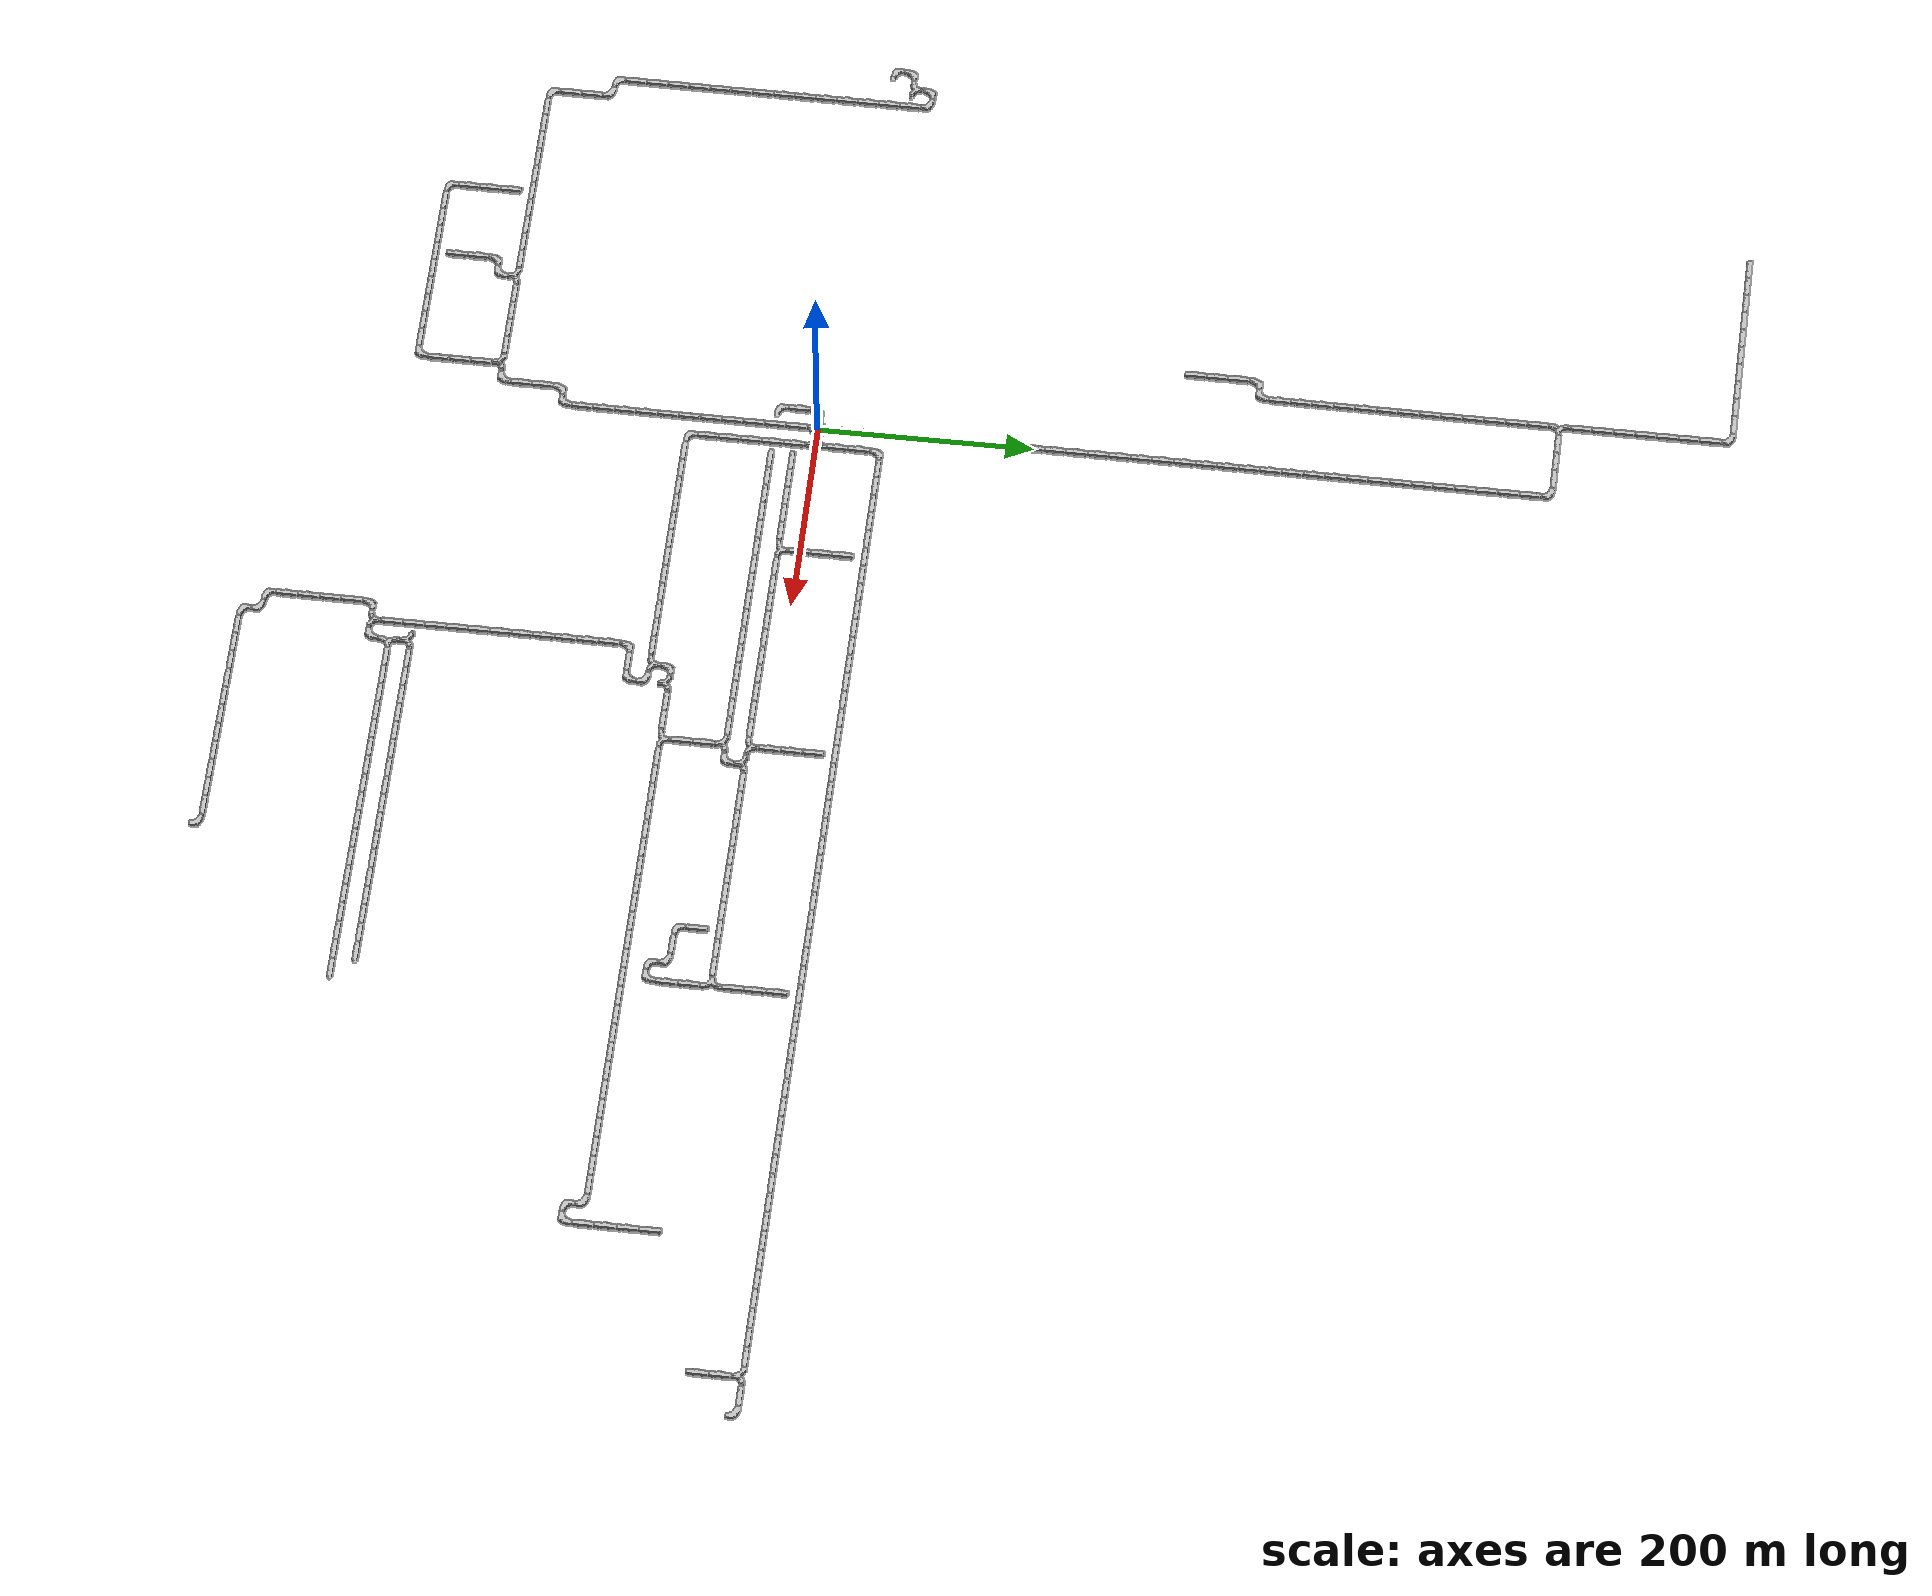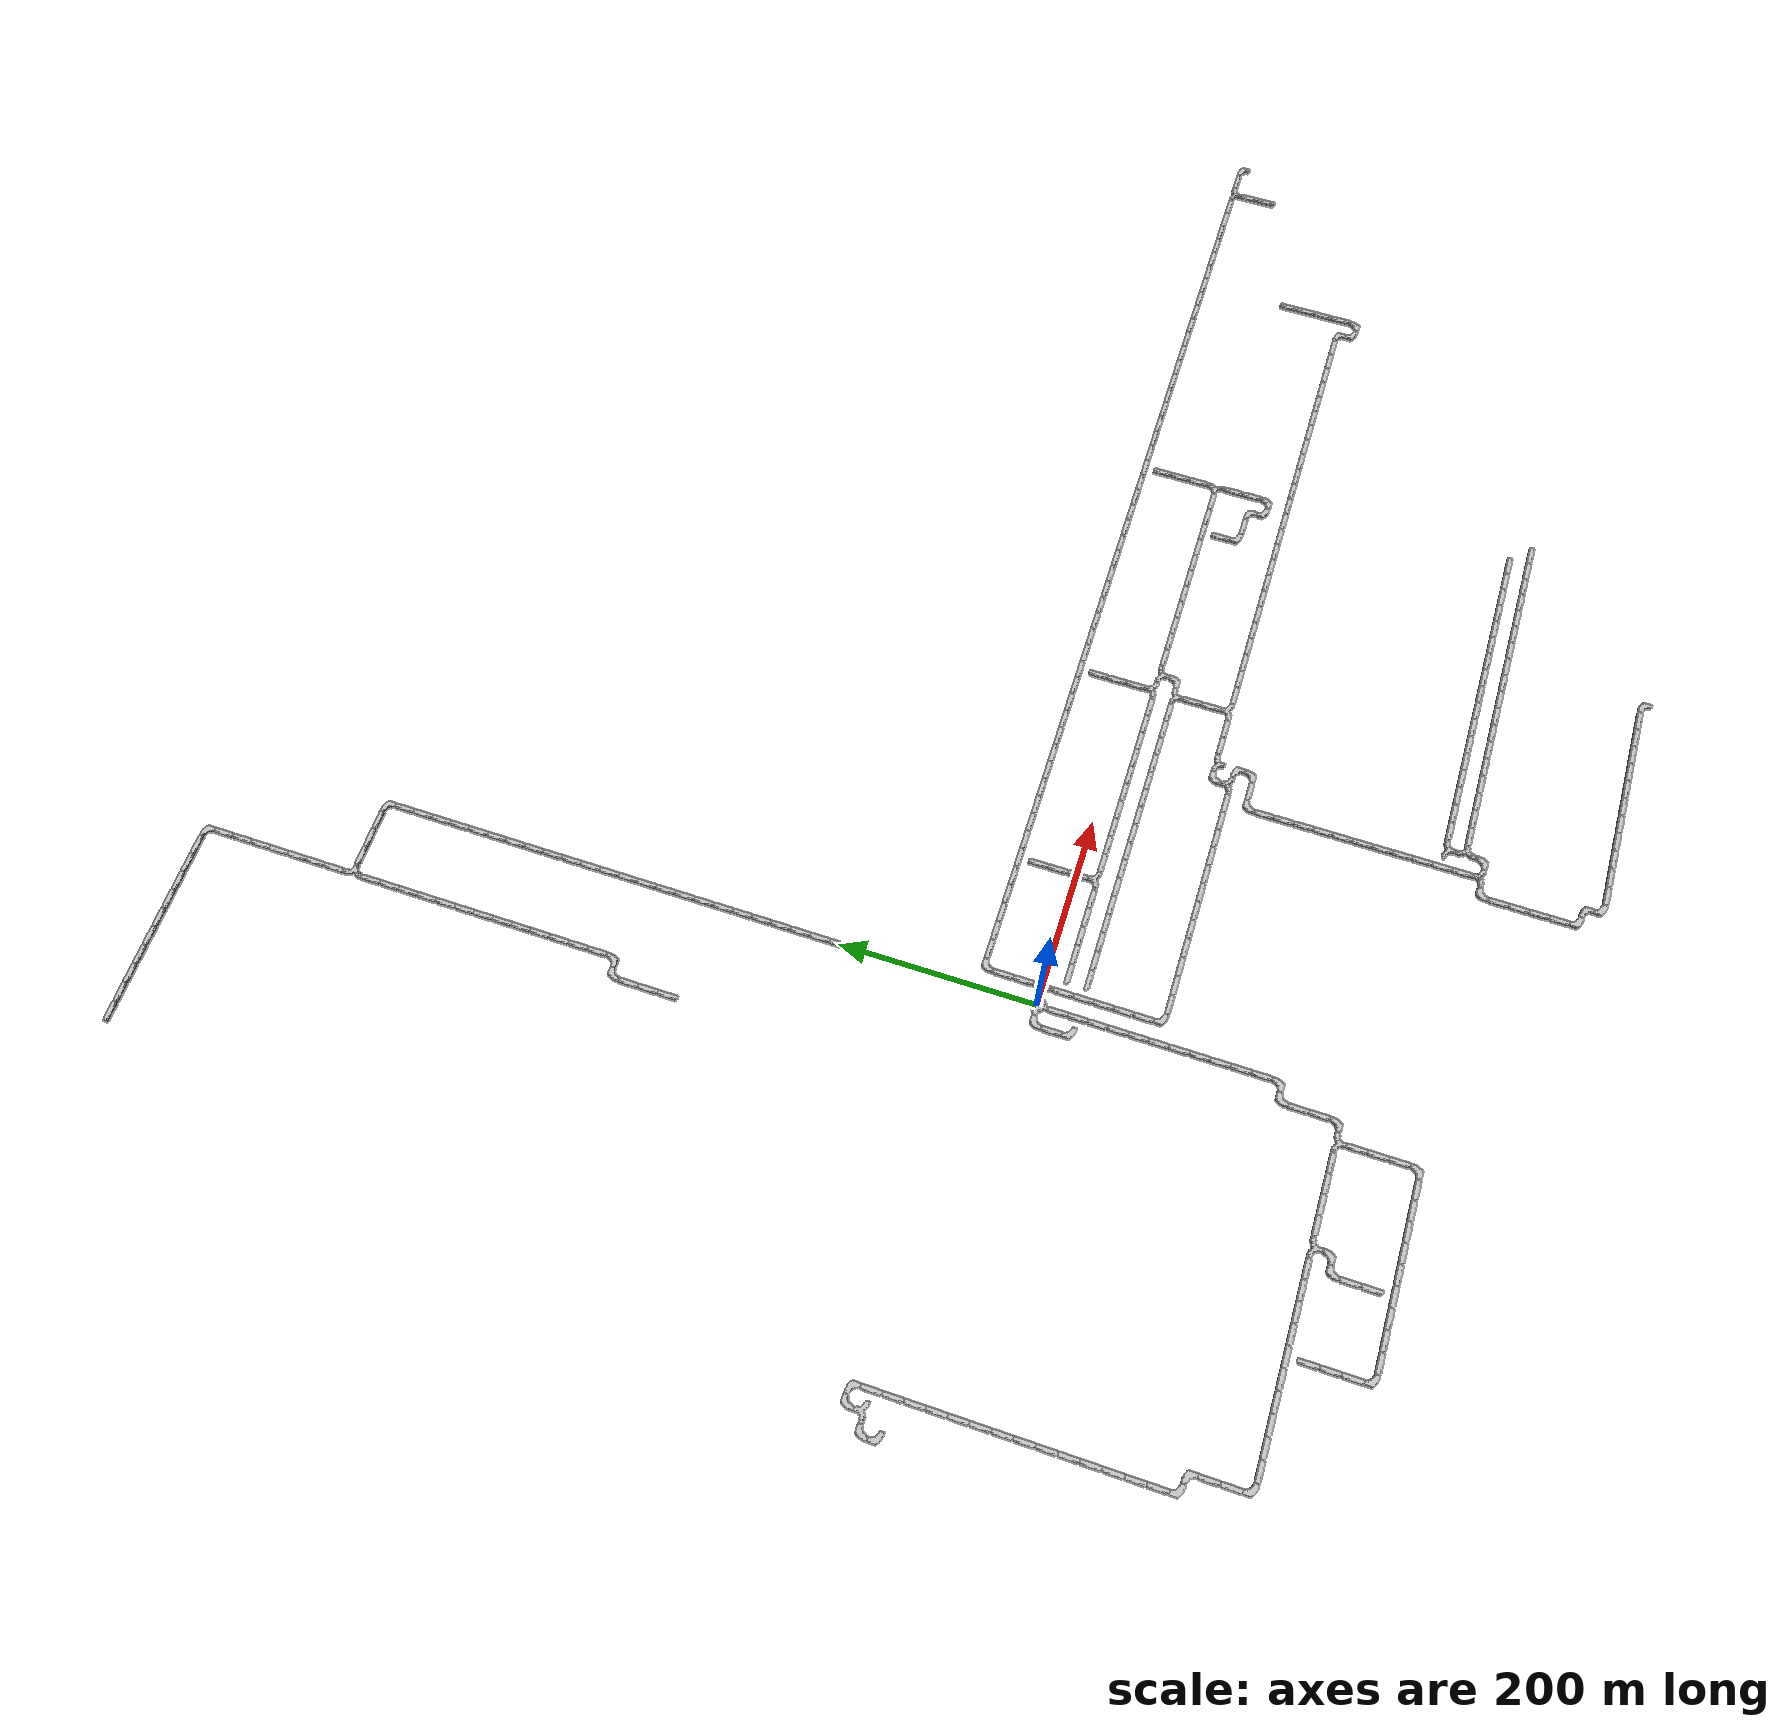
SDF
<sdf version="1.6">
 <world name="cave_8000_16">
  <include>
   <static>true</static>
   <name>cave_0_0</name>
   <pose>0 0 0 0 0 -1.5707963267948966</pose>
   <uri>model://cave_4way_20m</uri>
  </include>
  <include>
   <static>true</static>
   <name>cave_1_0</name>
   <pose>20 0 0 0 0 1.5707963267948966</pose>
   <uri>model://cave_3way_20m</uri>
  </include>
  <include>
   <static>true</static>
   <name>cave_1_-1</name>
   <pose>20 -20 0 0 0 0.0</pose>
   <uri>model://cave_straight_20m</uri>
  </include>
  <include>
   <static>true</static>
   <name>cave_1_-2</name>
   <pose>20 -40 0 0 0 0.0</pose>
   <uri>model://cave_straight_20m</uri>
  </include>
  <include>
   <static>true</static>
   <name>cave_1_-3</name>
   <pose>20 -60 0 0 0 0.0</pose>
   <uri>model://cave_straight_20m</uri>
  </include>
  <include>
   <static>true</static>
   <name>cave_1_-4</name>
   <pose>20 -80 0 0 0 0.0</pose>
   <uri>model://cave_straight_20m</uri>
  </include>
  <include>
   <static>true</static>
   <name>cave_1_-5</name>
   <pose>20 -100 0 0 0 0.0</pose>
   <uri>model://cave_straight_20m</uri>
  </include>
  <include>
   <static>true</static>
   <name>cave_1_-6</name>
   <pose>20 -120 0 0 0 0.0</pose>
   <uri>model://cave_L_20m</uri>
  </include>
  <include>
   <static>true</static>
   <name>cave_2_-6</name>
   <pose>40 -120 0 0 0 1.5707963267948966</pose>
   <uri>model://cave_straight_20m</uri>
  </include>
  <include>
   <static>true</static>
   <name>cave_3_-6</name>
   <pose>60 -120 0 0 0 1.5707963267948966</pose>
   <uri>model://cave_straight_20m</uri>
  </include>
  <include>
   <static>true</static>
   <name>cave_4_-6</name>
   <pose>80 -120 0 0 0 1.5707963267948966</pose>
   <uri>model://cave_straight_20m</uri>
  </include>
  <include>
   <static>true</static>
   <name>cave_5_-6</name>
   <pose>100 -120 0 0 0 1.5707963267948966</pose>
   <uri>model://cave_straight_20m</uri>
  </include>
  <include>
   <static>true</static>
   <name>cave_6_-6</name>
   <pose>120 -120 0 0 0 1.5707963267948966</pose>
   <uri>model://cave_straight_20m</uri>
  </include>
  <include>
   <static>true</static>
   <name>cave_7_-6</name>
   <pose>140 -120 0 0 0 1.5707963267948966</pose>
   <uri>model://cave_straight_20m</uri>
  </include>
  <include>
   <static>true</static>
   <name>cave_8_-6</name>
   <pose>160 -120 0 0 0 1.5707963267948966</pose>
   <uri>model://cave_straight_20m</uri>
  </include>
  <include>
   <static>true</static>
   <name>cave_9_-6</name>
   <pose>180 -120 0 0 0 1.5707963267948966</pose>
   <uri>model://cave_straight_20m</uri>
  </include>
  <include>
   <static>true</static>
   <name>cave_10_-6</name>
   <pose>200 -120 0 0 0 1.5707963267948966</pose>
   <uri>model://cave_straight_20m</uri>
  </include>
  <include>
   <static>true</static>
   <name>cave_11_-6</name>
   <pose>220 -120 0 0 0 1.5707963267948966</pose>
   <uri>model://cave_straight_20m</uri>
  </include>
  <include>
   <static>true</static>
   <name>cave_12_-6</name>
   <pose>240 -120 0 0 0 1.5707963267948966</pose>
   <uri>model://cave_straight_20m</uri>
  </include>
  <include>
   <static>true</static>
   <name>cave_13_-6</name>
   <pose>260 -120 0 0 0 1.5707963267948966</pose>
   <uri>model://cave_straight_20m</uri>
  </include>
  <include>
   <static>true</static>
   <name>cave_14_-6</name>
   <pose>280 -120 0 0 0 0.0</pose>
   <uri>model://cave_3way_20m</uri>
  </include>
  <include>
   <static>true</static>
   <name>cave_15_-6</name>
   <pose>300 -120 0 0 0 3.141592653589793</pose>
   <uri>model://cave_L_20m</uri>
  </include>
  <include>
   <static>true</static>
   <name>cave_15_-7</name>
   <pose>300 -140 0 0 0 1.5707963267948966</pose>
   <uri>model://cave_L_20m</uri>
  </include>
  <include>
   <static>true</static>
   <name>cave_14_-7</name>
   <pose>280 -140 0 0 0 1.5707963267948966</pose>
   <uri>model://cave_straight_20m</uri>
  </include>
  <include>
   <static>true</static>
   <name>cave_13_-7</name>
   <pose>260 -140 0 0 0 -1.5707963267948966</pose>
   <uri>model://cave_L_20m</uri>
  </include>
  <include>
   <static>true</static>
   <name>cave_13_-8</name>
   <pose>260 -160 0 0 0 0.0</pose>
   <uri>model://cave_straight_20m</uri>
  </include>
  <include>
   <static>true</static>
   <name>cave_13_-9</name>
   <pose>260 -180 0 0 0 0.0</pose>
   <uri>model://cave_straight_20m</uri>
  </include>
  <include>
   <static>true</static>
   <name>cave_13_-10</name>
   <pose>260 -200 0 0 0 0.0</pose>
   <uri>model://cave_straight_20m</uri>
  </include>
  <include>
   <static>true</static>
   <name>cave_13_-11</name>
   <pose>260 -220 0 0 0 0.0</pose>
   <uri>model://cave_straight_20m</uri>
  </include>
  <include>
   <static>true</static>
   <name>cave_13_-12</name>
   <pose>260 -240 0 0 0 0.0</pose>
   <uri>model://cave_straight_20m</uri>
  </include>
  <include>
   <static>true</static>
   <name>cave_13_-13</name>
   <pose>260 -260 0 0 0 0.0</pose>
   <uri>model://cave_straight_20m</uri>
  </include>
  <include>
   <static>true</static>
   <name>cave_13_-14</name>
   <pose>260 -280 0 0 0 0.0</pose>
   <uri>model://cave_straight_20m</uri>
  </include>
  <include>
   <static>true</static>
   <name>cave_13_-15</name>
   <pose>260 -300 0 0 0 0.0</pose>
   <uri>model://cave_straight_20m</uri>
  </include>
  <include>
   <static>true</static>
   <name>cave_13_-16</name>
   <pose>260 -320 0 0 0 0.0</pose>
   <uri>model://cave_straight_20m</uri>
  </include>
  <include>
   <static>true</static>
   <name>cave_13_-17</name>
   <pose>260 -340 0 0 0 0.0</pose>
   <uri>model://cave_straight_20m</uri>
  </include>
  <include>
   <static>true</static>
   <name>cave_13_-18</name>
   <pose>260 -360 0 0 0 0.0</pose>
   <uri>model://cave_straight_20m</uri>
  </include>
  <include>
   <static>true</static>
   <name>cave_13_-19</name>
   <pose>260 -380 0 0 0 0.0</pose>
   <uri>model://cave_3way_20m</uri>
  </include>
  <include>
   <static>true</static>
   <name>cave_14_-19</name>
   <pose>280 -380 0 0 0 1.5707963267948966</pose>
   <uri>model://cave_L_20m</uri>
  </include>
  <include>
   <static>true</static>
   <name>cave_14_-18</name>
   <pose>280 -360 0 0 0 -1.5707963267948966</pose>
   <uri>model://cave_3way_20m</uri>
  </include>
  <include>
   <static>true</static>
   <name>cave_15_-18</name>
   <pose>300 -360 0 0 0 1.5707963267948966</pose>
   <uri>model://cave_straight_20m</uri>
  </include>
  <include>
   <static>true</static>
   <name>cave_16_-18</name>
   <pose>320 -360 0 0 0 1.5707963267948966</pose>
   <uri>model://cave_straight_20m</uri>
  </include>
  <include>
   <static>true</static>
   <name>cave_17_-18</name>
   <pose>340 -360 0 0 0 1.5707963267948966</pose>
   <uri>model://cave_straight_20m</uri>
  </include>
  <include>
   <static>true</static>
   <name>cave_18_-18</name>
   <pose>360 -360 0 0 0 1.5707963267948966</pose>
   <uri>model://cave_straight_20m</uri>
  </include>
  <include>
   <static>true</static>
   <name>cave_19_-18</name>
   <pose>380 -360 0 0 0 1.5707963267948966</pose>
   <uri>model://cave_straight_20m</uri>
  </include>
  <include>
   <static>true</static>
   <name>cave_20_-18</name>
   <pose>400 -360 0 0 0 1.5707963267948966</pose>
   <uri>model://cave_straight_20m</uri>
  </include>
  <include>
   <static>true</static>
   <name>cave_21_-18</name>
   <pose>420 -360 0 0 0 1.5707963267948966</pose>
   <uri>model://cave_straight_20m</uri>
  </include>
  <include>
   <static>true</static>
   <name>cave_22_-18</name>
   <pose>440 -360 0 0 0 1.5707963267948966</pose>
   <uri>model://cave_straight_20m</uri>
  </include>
  <include>
   <static>true</static>
   <name>cave_23_-18</name>
   <pose>460 -360 0 0 0 1.5707963267948966</pose>
   <uri>model://cave_straight_20m</uri>
  </include>
  <include>
   <static>true</static>
   <name>cave_24_-18</name>
   <pose>480 -360 0 0 0 1.5707963267948966</pose>
   <uri>model://cave_straight_20m</uri>
  </include>
  <include>
   <static>true</static>
   <name>cave_25_-18</name>
   <pose>500 -360 0 0 0 1.5707963267948966</pose>
   <uri>model://cave_straight_20m</uri>
  </include>
  <include>
   <static>true</static>
   <name>cave_26_-18</name>
   <pose>520 -360 0 0 0 1.5707963267948966</pose>
   <uri>model://cave_straight_20m</uri>
  </include>
  <include>
   <static>true</static>
   <name>cave_27_-18</name>
   <pose>540 -360 0 0 0 1.5707963267948966</pose>
   <uri>model://cave_straight_20m</uri>
  </include>
  <include>
   <static>true</static>
   <name>cave_28_-18</name>
   <pose>560 -360 0 0 0 1.5707963267948966</pose>
   <uri>model://cave_straight_20m</uri>
  </include>
  <include>
   <static>true</static>
   <name>cave_29_-18</name>
   <pose>580 -360 0 0 0 1.5707963267948966</pose>
   <uri>model://cave_straight_20m</uri>
  </include>
  <include>
   <static>true</static>
   <name>cave_30_-18</name>
   <pose>600 -360 0 0 0 1.5707963267948966</pose>
   <uri>model://cave_straight_20m</uri>
  </include>
  <include>
   <static>true</static>
   <name>cave_31_-18</name>
   <pose>620 -360 0 0 0 1.5707963267948966</pose>
   <uri>model://cave_straight_20m</uri>
  </include>
  <include>
   <static>true</static>
   <name>cave_32_-18</name>
   <pose>640 -360 0 0 0 1.5707963267948966</pose>
   <uri>model://cave_straight_20m</uri>
  </include>
  <include>
   <static>true</static>
   <name>cave_14_-17</name>
   <pose>280 -340 0 0 0 3.141592653589793</pose>
   <uri>model://cave_3way_20m</uri>
  </include>
  <include>
   <static>true</static>
   <name>cave_15_-17</name>
   <pose>300 -340 0 0 0 1.5707963267948966</pose>
   <uri>model://cave_straight_20m</uri>
  </include>
  <include>
   <static>true</static>
   <name>cave_16_-17</name>
   <pose>320 -340 0 0 0 1.5707963267948966</pose>
   <uri>model://cave_straight_20m</uri>
  </include>
  <include>
   <static>true</static>
   <name>cave_17_-17</name>
   <pose>340 -340 0 0 0 1.5707963267948966</pose>
   <uri>model://cave_straight_20m</uri>
  </include>
  <include>
   <static>true</static>
   <name>cave_18_-17</name>
   <pose>360 -340 0 0 0 1.5707963267948966</pose>
   <uri>model://cave_straight_20m</uri>
  </include>
  <include>
   <static>true</static>
   <name>cave_19_-17</name>
   <pose>380 -340 0 0 0 1.5707963267948966</pose>
   <uri>model://cave_straight_20m</uri>
  </include>
  <include>
   <static>true</static>
   <name>cave_20_-17</name>
   <pose>400 -340 0 0 0 1.5707963267948966</pose>
   <uri>model://cave_straight_20m</uri>
  </include>
  <include>
   <static>true</static>
   <name>cave_21_-17</name>
   <pose>420 -340 0 0 0 1.5707963267948966</pose>
   <uri>model://cave_straight_20m</uri>
  </include>
  <include>
   <static>true</static>
   <name>cave_22_-17</name>
   <pose>440 -340 0 0 0 1.5707963267948966</pose>
   <uri>model://cave_straight_20m</uri>
  </include>
  <include>
   <static>true</static>
   <name>cave_23_-17</name>
   <pose>460 -340 0 0 0 1.5707963267948966</pose>
   <uri>model://cave_straight_20m</uri>
  </include>
  <include>
   <static>true</static>
   <name>cave_24_-17</name>
   <pose>480 -340 0 0 0 1.5707963267948966</pose>
   <uri>model://cave_straight_20m</uri>
  </include>
  <include>
   <static>true</static>
   <name>cave_25_-17</name>
   <pose>500 -340 0 0 0 1.5707963267948966</pose>
   <uri>model://cave_straight_20m</uri>
  </include>
  <include>
   <static>true</static>
   <name>cave_26_-17</name>
   <pose>520 -340 0 0 0 1.5707963267948966</pose>
   <uri>model://cave_straight_20m</uri>
  </include>
  <include>
   <static>true</static>
   <name>cave_27_-17</name>
   <pose>540 -340 0 0 0 1.5707963267948966</pose>
   <uri>model://cave_straight_20m</uri>
  </include>
  <include>
   <static>true</static>
   <name>cave_28_-17</name>
   <pose>560 -340 0 0 0 1.5707963267948966</pose>
   <uri>model://cave_straight_20m</uri>
  </include>
  <include>
   <static>true</static>
   <name>cave_29_-17</name>
   <pose>580 -340 0 0 0 1.5707963267948966</pose>
   <uri>model://cave_straight_20m</uri>
  </include>
  <include>
   <static>true</static>
   <name>cave_30_-17</name>
   <pose>600 -340 0 0 0 1.5707963267948966</pose>
   <uri>model://cave_straight_20m</uri>
  </include>
  <include>
   <static>true</static>
   <name>cave_31_-17</name>
   <pose>620 -340 0 0 0 1.5707963267948966</pose>
   <uri>model://cave_straight_20m</uri>
  </include>
  <include>
   <static>true</static>
   <name>cave_12_-19</name>
   <pose>240 -380 0 0 0 -1.5707963267948966</pose>
   <uri>model://cave_L_20m</uri>
  </include>
  <include>
   <static>true</static>
   <name>cave_12_-20</name>
   <pose>240 -400 0 0 0 0.0</pose>
   <uri>model://cave_straight_20m</uri>
  </include>
  <include>
   <static>true</static>
   <name>cave_12_-21</name>
   <pose>240 -420 0 0 0 0.0</pose>
   <uri>model://cave_straight_20m</uri>
  </include>
  <include>
   <static>true</static>
   <name>cave_12_-22</name>
   <pose>240 -440 0 0 0 0.0</pose>
   <uri>model://cave_straight_20m</uri>
  </include>
  <include>
   <static>true</static>
   <name>cave_12_-23</name>
   <pose>240 -460 0 0 0 0.0</pose>
   <uri>model://cave_straight_20m</uri>
  </include>
  <include>
   <static>true</static>
   <name>cave_12_-24</name>
   <pose>240 -480 0 0 0 0.0</pose>
   <uri>model://cave_L_20m</uri>
  </include>
  <include>
   <static>true</static>
   <name>cave_13_-24</name>
   <pose>260 -480 0 0 0 3.141592653589793</pose>
   <uri>model://cave_L_20m</uri>
  </include>
  <include>
   <static>true</static>
   <name>cave_13_-25</name>
   <pose>260 -500 0 0 0 0.0</pose>
   <uri>model://cave_L_20m</uri>
  </include>
  <include>
   <static>true</static>
   <name>cave_14_-25</name>
   <pose>280 -500 0 0 0 1.5707963267948966</pose>
   <uri>model://cave_straight_20m</uri>
  </include>
  <include>
   <static>true</static>
   <name>cave_15_-25</name>
   <pose>300 -500 0 0 0 1.5707963267948966</pose>
   <uri>model://cave_straight_20m</uri>
  </include>
  <include>
   <static>true</static>
   <name>cave_16_-25</name>
   <pose>320 -500 0 0 0 1.5707963267948966</pose>
   <uri>model://cave_straight_20m</uri>
  </include>
  <include>
   <static>true</static>
   <name>cave_17_-25</name>
   <pose>340 -500 0 0 0 1.5707963267948966</pose>
   <uri>model://cave_straight_20m</uri>
  </include>
  <include>
   <static>true</static>
   <name>cave_18_-25</name>
   <pose>360 -500 0 0 0 1.5707963267948966</pose>
   <uri>model://cave_straight_20m</uri>
  </include>
  <include>
   <static>true</static>
   <name>cave_19_-25</name>
   <pose>380 -500 0 0 0 1.5707963267948966</pose>
   <uri>model://cave_straight_20m</uri>
  </include>
  <include>
   <static>true</static>
   <name>cave_20_-25</name>
   <pose>400 -500 0 0 0 1.5707963267948966</pose>
   <uri>model://cave_straight_20m</uri>
  </include>
  <include>
   <static>true</static>
   <name>cave_21_-25</name>
   <pose>420 -500 0 0 0 1.5707963267948966</pose>
   <uri>model://cave_straight_20m</uri>
  </include>
  <include>
   <static>true</static>
   <name>cave_22_-25</name>
   <pose>440 -500 0 0 0 1.5707963267948966</pose>
   <uri>model://cave_straight_20m</uri>
  </include>
  <include>
   <static>true</static>
   <name>cave_23_-25</name>
   <pose>460 -500 0 0 0 1.5707963267948966</pose>
   <uri>model://cave_straight_20m</uri>
  </include>
  <include>
   <static>true</static>
   <name>cave_24_-25</name>
   <pose>480 -500 0 0 0 1.5707963267948966</pose>
   <uri>model://cave_straight_20m</uri>
  </include>
  <include>
   <static>true</static>
   <name>cave_25_-25</name>
   <pose>500 -500 0 0 0 3.141592653589793</pose>
   <uri>model://cave_L_20m</uri>
  </include>
  <include>
   <static>true</static>
   <name>cave_14_-5</name>
   <pose>280 -100 0 0 0 -1.5707963267948966</pose>
   <uri>model://cave_L_20m</uri>
  </include>
  <include>
   <static>true</static>
   <name>cave_15_-5</name>
   <pose>300 -100 0 0 0 3.141592653589793</pose>
   <uri>model://cave_3way_20m</uri>
  </include>
  <include>
   <static>true</static>
   <name>cave_16_-5</name>
   <pose>320 -100 0 0 0 1.5707963267948966</pose>
   <uri>model://cave_straight_20m</uri>
  </include>
  <include>
   <static>true</static>
   <name>cave_17_-5</name>
   <pose>340 -100 0 0 0 1.5707963267948966</pose>
   <uri>model://cave_straight_20m</uri>
  </include>
  <include>
   <static>true</static>
   <name>cave_18_-5</name>
   <pose>360 -100 0 0 0 0.0</pose>
   <uri>model://cave_3way_20m</uri>
  </include>
  <include>
   <static>true</static>
   <name>cave_19_-5</name>
   <pose>380 -100 0 0 0 1.5707963267948966</pose>
   <uri>model://cave_straight_20m</uri>
  </include>
  <include>
   <static>true</static>
   <name>cave_20_-5</name>
   <pose>400 -100 0 0 0 1.5707963267948966</pose>
   <uri>model://cave_straight_20m</uri>
  </include>
  <include>
   <static>true</static>
   <name>cave_21_-5</name>
   <pose>420 -100 0 0 0 1.5707963267948966</pose>
   <uri>model://cave_straight_20m</uri>
  </include>
  <include>
   <static>true</static>
   <name>cave_22_-5</name>
   <pose>440 -100 0 0 0 1.5707963267948966</pose>
   <uri>model://cave_straight_20m</uri>
  </include>
  <include>
   <static>true</static>
   <name>cave_23_-5</name>
   <pose>460 -100 0 0 0 1.5707963267948966</pose>
   <uri>model://cave_straight_20m</uri>
  </include>
  <include>
   <static>true</static>
   <name>cave_24_-5</name>
   <pose>480 -100 0 0 0 1.5707963267948966</pose>
   <uri>model://cave_straight_20m</uri>
  </include>
  <include>
   <static>true</static>
   <name>cave_25_-5</name>
   <pose>500 -100 0 0 0 1.5707963267948966</pose>
   <uri>model://cave_straight_20m</uri>
  </include>
  <include>
   <static>true</static>
   <name>cave_26_-5</name>
   <pose>520 -100 0 0 0 1.5707963267948966</pose>
   <uri>model://cave_straight_20m</uri>
  </include>
  <include>
   <static>true</static>
   <name>cave_27_-5</name>
   <pose>540 -100 0 0 0 1.5707963267948966</pose>
   <uri>model://cave_straight_20m</uri>
  </include>
  <include>
   <static>true</static>
   <name>cave_28_-5</name>
   <pose>560 -100 0 0 0 1.5707963267948966</pose>
   <uri>model://cave_straight_20m</uri>
  </include>
  <include>
   <static>true</static>
   <name>cave_29_-5</name>
   <pose>580 -100 0 0 0 1.5707963267948966</pose>
   <uri>model://cave_straight_20m</uri>
  </include>
  <include>
   <static>true</static>
   <name>cave_30_-5</name>
   <pose>600 -100 0 0 0 1.5707963267948966</pose>
   <uri>model://cave_straight_20m</uri>
  </include>
  <include>
   <static>true</static>
   <name>cave_31_-5</name>
   <pose>620 -100 0 0 0 1.5707963267948966</pose>
   <uri>model://cave_straight_20m</uri>
  </include>
  <include>
   <static>true</static>
   <name>cave_32_-5</name>
   <pose>640 -100 0 0 0 1.5707963267948966</pose>
   <uri>model://cave_straight_20m</uri>
  </include>
  <include>
   <static>true</static>
   <name>cave_33_-5</name>
   <pose>660 -100 0 0 0 1.5707963267948966</pose>
   <uri>model://cave_straight_20m</uri>
  </include>
  <include>
   <static>true</static>
   <name>cave_34_-5</name>
   <pose>680 -100 0 0 0 1.5707963267948966</pose>
   <uri>model://cave_straight_20m</uri>
  </include>
  <include>
   <static>true</static>
   <name>cave_35_-5</name>
   <pose>700 -100 0 0 0 1.5707963267948966</pose>
   <uri>model://cave_straight_20m</uri>
  </include>
  <include>
   <static>true</static>
   <name>cave_36_-5</name>
   <pose>720 -100 0 0 0 1.5707963267948966</pose>
   <uri>model://cave_straight_20m</uri>
  </include>
  <include>
   <static>true</static>
   <name>cave_37_-5</name>
   <pose>740 -100 0 0 0 1.5707963267948966</pose>
   <uri>model://cave_straight_20m</uri>
  </include>
  <include>
   <static>true</static>
   <name>cave_38_-5</name>
   <pose>760 -100 0 0 0 1.5707963267948966</pose>
   <uri>model://cave_straight_20m</uri>
  </include>
  <include>
   <static>true</static>
   <name>cave_39_-5</name>
   <pose>780 -100 0 0 0 1.5707963267948966</pose>
   <uri>model://cave_straight_20m</uri>
  </include>
  <include>
   <static>true</static>
   <name>cave_40_-5</name>
   <pose>800 -100 0 0 0 1.5707963267948966</pose>
   <uri>model://cave_straight_20m</uri>
  </include>
  <include>
   <static>true</static>
   <name>cave_41_-5</name>
   <pose>820 -100 0 0 0 1.5707963267948966</pose>
   <uri>model://cave_straight_20m</uri>
  </include>
  <include>
   <static>true</static>
   <name>cave_42_-5</name>
   <pose>840 -100 0 0 0 1.5707963267948966</pose>
   <uri>model://cave_straight_20m</uri>
  </include>
  <include>
   <static>true</static>
   <name>cave_43_-5</name>
   <pose>860 -100 0 0 0 3.141592653589793</pose>
   <uri>model://cave_L_20m</uri>
  </include>
  <include>
   <static>true</static>
   <name>cave_43_-6</name>
   <pose>860 -120 0 0 0 0.0</pose>
   <uri>model://cave_L_20m</uri>
  </include>
  <include>
   <static>true</static>
   <name>cave_44_-6</name>
   <pose>880 -120 0 0 0 1.5707963267948966</pose>
   <uri>model://cave_L_20m</uri>
  </include>
  <include>
   <static>true</static>
   <name>cave_44_-5</name>
   <pose>880 -100 0 0 0 0.0</pose>
   <uri>model://cave_straight_20m</uri>
  </include>
  <include>
   <static>true</static>
   <name>cave_44_-4</name>
   <pose>880 -80 0 0 0 0.0</pose>
   <uri>model://cave_straight_20m</uri>
  </include>
  <include>
   <static>true</static>
   <name>cave_44_-3</name>
   <pose>880 -60 0 0 0 0.0</pose>
   <uri>model://cave_straight_20m</uri>
  </include>
  <include>
   <static>true</static>
   <name>cave_44_-2</name>
   <pose>880 -40 0 0 0 0.0</pose>
   <uri>model://cave_straight_20m</uri>
  </include>
  <include>
   <static>true</static>
   <name>cave_18_-4</name>
   <pose>360 -80 0 0 0 0.0</pose>
   <uri>model://cave_straight_20m</uri>
  </include>
  <include>
   <static>true</static>
   <name>cave_18_-3</name>
   <pose>360 -60 0 0 0 0.0</pose>
   <uri>model://cave_straight_20m</uri>
  </include>
  <include>
   <static>true</static>
   <name>cave_18_-2</name>
   <pose>360 -40 0 0 0 3.141592653589793</pose>
   <uri>model://cave_3way_20m</uri>
  </include>
  <include>
   <static>true</static>
   <name>cave_19_-2</name>
   <pose>380 -40 0 0 0 1.5707963267948966</pose>
   <uri>model://cave_L_20m</uri>
  </include>
  <include>
   <static>true</static>
   <name>cave_19_-1</name>
   <pose>380 -20 0 0 0 3.141592653589793</pose>
   <uri>model://cave_3way_20m</uri>
  </include>
  <include>
   <static>true</static>
   <name>cave_20_-1</name>
   <pose>400 -20 0 0 0 1.5707963267948966</pose>
   <uri>model://cave_straight_20m</uri>
  </include>
  <include>
   <static>true</static>
   <name>cave_21_-1</name>
   <pose>420 -20 0 0 0 1.5707963267948966</pose>
   <uri>model://cave_straight_20m</uri>
  </include>
  <include>
   <static>true</static>
   <name>cave_22_-1</name>
   <pose>440 -20 0 0 0 1.5707963267948966</pose>
   <uri>model://cave_straight_20m</uri>
  </include>
  <include>
   <static>true</static>
   <name>cave_23_-1</name>
   <pose>460 -20 0 0 0 1.5707963267948966</pose>
   <uri>model://cave_straight_20m</uri>
  </include>
  <include>
   <static>true</static>
   <name>cave_24_-1</name>
   <pose>480 -20 0 0 0 1.5707963267948966</pose>
   <uri>model://cave_straight_20m</uri>
  </include>
  <include>
   <static>true</static>
   <name>cave_25_-1</name>
   <pose>500 -20 0 0 0 1.5707963267948966</pose>
   <uri>model://cave_straight_20m</uri>
  </include>
  <include>
   <static>true</static>
   <name>cave_26_-1</name>
   <pose>520 -20 0 0 0 1.5707963267948966</pose>
   <uri>model://cave_straight_20m</uri>
  </include>
  <include>
   <static>true</static>
   <name>cave_27_-1</name>
   <pose>540 -20 0 0 0 1.5707963267948966</pose>
   <uri>model://cave_straight_20m</uri>
  </include>
  <include>
   <static>true</static>
   <name>cave_28_-1</name>
   <pose>560 -20 0 0 0 1.5707963267948966</pose>
   <uri>model://cave_straight_20m</uri>
  </include>
  <include>
   <static>true</static>
   <name>cave_29_-1</name>
   <pose>580 -20 0 0 0 1.5707963267948966</pose>
   <uri>model://cave_straight_20m</uri>
  </include>
  <include>
   <static>true</static>
   <name>cave_30_-1</name>
   <pose>600 -20 0 0 0 1.5707963267948966</pose>
   <uri>model://cave_straight_20m</uri>
  </include>
  <include>
   <static>true</static>
   <name>cave_31_-1</name>
   <pose>620 -20 0 0 0 1.5707963267948966</pose>
   <uri>model://cave_3way_20m</uri>
  </include>
  <include>
   <static>true</static>
   <name>cave_31_-2</name>
   <pose>620 -40 0 0 0 0.0</pose>
   <uri>model://cave_straight_20m</uri>
  </include>
  <include>
   <static>true</static>
   <name>cave_31_-3</name>
   <pose>620 -60 0 0 0 0.0</pose>
   <uri>model://cave_straight_20m</uri>
  </include>
  <include>
   <static>true</static>
   <name>cave_31_-4</name>
   <pose>620 -80 0 0 0 1.5707963267948966</pose>
   <uri>model://cave_L_20m</uri>
  </include>
  <include>
   <static>true</static>
   <name>cave_30_-4</name>
   <pose>600 -80 0 0 0 0.0</pose>
   <uri>model://cave_L_20m</uri>
  </include>
  <include>
   <static>true</static>
   <name>cave_30_-3</name>
   <pose>600 -60 0 0 0 3.141592653589793</pose>
   <uri>model://cave_L_20m</uri>
  </include>
  <include>
   <static>true</static>
   <name>cave_29_-3</name>
   <pose>580 -60 0 0 0 1.5707963267948966</pose>
   <uri>model://cave_straight_20m</uri>
  </include>
  <include>
   <static>true</static>
   <name>cave_28_-3</name>
   <pose>560 -60 0 0 0 0.0</pose>
   <uri>model://cave_L_20m</uri>
  </include>
  <include>
   <static>true</static>
   <name>cave_28_-2</name>
   <pose>560 -40 0 0 0 0.0</pose>
   <uri>model://cave_straight_20m</uri>
  </include>
  <include>
   <static>true</static>
   <name>cave_31_0</name>
   <pose>620 0 0 0 0 0.0</pose>
   <uri>model://cave_straight_20m</uri>
  </include>
  <include>
   <static>true</static>
   <name>cave_31_1</name>
   <pose>620 20 0 0 0 0.0</pose>
   <uri>model://cave_straight_20m</uri>
  </include>
  <include>
   <static>true</static>
   <name>cave_31_2</name>
   <pose>620 40 0 0 0 0.0</pose>
   <uri>model://cave_straight_20m</uri>
  </include>
  <include>
   <static>true</static>
   <name>cave_18_-1</name>
   <pose>360 -20 0 0 0 0.0</pose>
   <uri>model://cave_3way_20m</uri>
  </include>
  <include>
   <static>true</static>
   <name>cave_17_-1</name>
   <pose>340 -20 0 0 0 1.5707963267948966</pose>
   <uri>model://cave_straight_20m</uri>
  </include>
  <include>
   <static>true</static>
   <name>cave_16_-1</name>
   <pose>320 -20 0 0 0 1.5707963267948966</pose>
   <uri>model://cave_straight_20m</uri>
  </include>
  <include>
   <static>true</static>
   <name>cave_15_-1</name>
   <pose>300 -20 0 0 0 1.5707963267948966</pose>
   <uri>model://cave_straight_20m</uri>
  </include>
  <include>
   <static>true</static>
   <name>cave_14_-1</name>
   <pose>280 -20 0 0 0 1.5707963267948966</pose>
   <uri>model://cave_straight_20m</uri>
  </include>
  <include>
   <static>true</static>
   <name>cave_13_-1</name>
   <pose>260 -20 0 0 0 1.5707963267948966</pose>
   <uri>model://cave_straight_20m</uri>
  </include>
  <include>
   <static>true</static>
   <name>cave_12_-1</name>
   <pose>240 -20 0 0 0 1.5707963267948966</pose>
   <uri>model://cave_straight_20m</uri>
  </include>
  <include>
   <static>true</static>
   <name>cave_11_-1</name>
   <pose>220 -20 0 0 0 1.5707963267948966</pose>
   <uri>model://cave_straight_20m</uri>
  </include>
  <include>
   <static>true</static>
   <name>cave_10_-1</name>
   <pose>200 -20 0 0 0 1.5707963267948966</pose>
   <uri>model://cave_straight_20m</uri>
  </include>
  <include>
   <static>true</static>
   <name>cave_9_-1</name>
   <pose>180 -20 0 0 0 1.5707963267948966</pose>
   <uri>model://cave_straight_20m</uri>
  </include>
  <include>
   <static>true</static>
   <name>cave_8_-1</name>
   <pose>160 -20 0 0 0 1.5707963267948966</pose>
   <uri>model://cave_straight_20m</uri>
  </include>
  <include>
   <static>true</static>
   <name>cave_7_-1</name>
   <pose>140 -20 0 0 0 0.0</pose>
   <uri>model://cave_3way_20m</uri>
  </include>
  <include>
   <static>true</static>
   <name>cave_6_-1</name>
   <pose>120 -20 0 0 0 1.5707963267948966</pose>
   <uri>model://cave_straight_20m</uri>
  </include>
  <include>
   <static>true</static>
   <name>cave_5_-1</name>
   <pose>100 -20 0 0 0 1.5707963267948966</pose>
   <uri>model://cave_straight_20m</uri>
  </include>
  <include>
   <static>true</static>
   <name>cave_4_-1</name>
   <pose>80 -20 0 0 0 1.5707963267948966</pose>
   <uri>model://cave_straight_20m</uri>
  </include>
  <include>
   <static>true</static>
   <name>cave_3_-1</name>
   <pose>60 -20 0 0 0 1.5707963267948966</pose>
   <uri>model://cave_straight_20m</uri>
  </include>
  <include>
   <static>true</static>
   <name>cave_2_-1</name>
   <pose>40 -20 0 0 0 1.5707963267948966</pose>
   <uri>model://cave_straight_20m</uri>
  </include>
  <include>
   <static>true</static>
   <name>cave_7_0</name>
   <pose>140 0 0 0 0 0.0</pose>
   <uri>model://cave_straight_20m</uri>
  </include>
  <include>
   <static>true</static>
   <name>cave_7_1</name>
   <pose>140 20 0 0 0 0.0</pose>
   <uri>model://cave_straight_20m</uri>
  </include>
  <include>
   <static>true</static>
   <name>cave_7_2</name>
   <pose>140 40 0 0 0 0.0</pose>
   <uri>model://cave_straight_20m</uri>
  </include>
  <include>
   <static>true</static>
   <name>cave_18_0</name>
   <pose>360 0 0 0 0 0.0</pose>
   <uri>model://cave_straight_20m</uri>
  </include>
  <include>
   <static>true</static>
   <name>cave_18_1</name>
   <pose>360 20 0 0 0 0.0</pose>
   <uri>model://cave_straight_20m</uri>
  </include>
  <include>
   <static>true</static>
   <name>cave_18_2</name>
   <pose>360 40 0 0 0 0.0</pose>
   <uri>model://cave_straight_20m</uri>
  </include>
  <include>
   <static>true</static>
   <name>cave_17_-2</name>
   <pose>340 -40 0 0 0 1.5707963267948966</pose>
   <uri>model://cave_straight_20m</uri>
  </include>
  <include>
   <static>true</static>
   <name>cave_16_-2</name>
   <pose>320 -40 0 0 0 1.5707963267948966</pose>
   <uri>model://cave_straight_20m</uri>
  </include>
  <include>
   <static>true</static>
   <name>cave_15_-2</name>
   <pose>300 -40 0 0 0 1.5707963267948966</pose>
   <uri>model://cave_straight_20m</uri>
  </include>
  <include>
   <static>true</static>
   <name>cave_14_-2</name>
   <pose>280 -40 0 0 0 1.5707963267948966</pose>
   <uri>model://cave_straight_20m</uri>
  </include>
  <include>
   <static>true</static>
   <name>cave_13_-2</name>
   <pose>260 -40 0 0 0 1.5707963267948966</pose>
   <uri>model://cave_straight_20m</uri>
  </include>
  <include>
   <static>true</static>
   <name>cave_12_-2</name>
   <pose>240 -40 0 0 0 1.5707963267948966</pose>
   <uri>model://cave_straight_20m</uri>
  </include>
  <include>
   <static>true</static>
   <name>cave_11_-2</name>
   <pose>220 -40 0 0 0 1.5707963267948966</pose>
   <uri>model://cave_straight_20m</uri>
  </include>
  <include>
   <static>true</static>
   <name>cave_10_-2</name>
   <pose>200 -40 0 0 0 1.5707963267948966</pose>
   <uri>model://cave_straight_20m</uri>
  </include>
  <include>
   <static>true</static>
   <name>cave_9_-2</name>
   <pose>180 -40 0 0 0 1.5707963267948966</pose>
   <uri>model://cave_straight_20m</uri>
  </include>
  <include>
   <static>true</static>
   <name>cave_8_-2</name>
   <pose>160 -40 0 0 0 1.5707963267948966</pose>
   <uri>model://cave_straight_20m</uri>
  </include>
  <include>
   <static>true</static>
   <name>cave_7_-2</name>
   <pose>140 -40 0 0 0 1.5707963267948966</pose>
   <uri>model://cave_straight_20m</uri>
  </include>
  <include>
   <static>true</static>
   <name>cave_6_-2</name>
   <pose>120 -40 0 0 0 1.5707963267948966</pose>
   <uri>model://cave_straight_20m</uri>
  </include>
  <include>
   <static>true</static>
   <name>cave_5_-2</name>
   <pose>100 -40 0 0 0 1.5707963267948966</pose>
   <uri>model://cave_straight_20m</uri>
  </include>
  <include>
   <static>true</static>
   <name>cave_4_-2</name>
   <pose>80 -40 0 0 0 1.5707963267948966</pose>
   <uri>model://cave_straight_20m</uri>
  </include>
  <include>
   <static>true</static>
   <name>cave_3_-2</name>
   <pose>60 -40 0 0 0 1.5707963267948966</pose>
   <uri>model://cave_straight_20m</uri>
  </include>
  <include>
   <static>true</static>
   <name>cave_2_-2</name>
   <pose>40 -40 0 0 0 1.5707963267948966</pose>
   <uri>model://cave_straight_20m</uri>
  </include>
  <include>
   <static>true</static>
   <name>cave_1_1</name>
   <pose>20 20 0 0 0 0.0</pose>
   <uri>model://cave_straight_20m</uri>
  </include>
  <include>
   <static>true</static>
   <name>cave_1_2</name>
   <pose>20 40 0 0 0 0.0</pose>
   <uri>model://cave_straight_20m</uri>
  </include>
  <include>
   <static>true</static>
   <name>cave_1_3</name>
   <pose>20 60 0 0 0 -1.5707963267948966</pose>
   <uri>model://cave_L_20m</uri>
  </include>
  <include>
   <static>true</static>
   <name>cave_2_3</name>
   <pose>40 60 0 0 0 1.5707963267948966</pose>
   <uri>model://cave_straight_20m</uri>
  </include>
  <include>
   <static>true</static>
   <name>cave_3_3</name>
   <pose>60 60 0 0 0 1.5707963267948966</pose>
   <uri>model://cave_straight_20m</uri>
  </include>
  <include>
   <static>true</static>
   <name>cave_4_3</name>
   <pose>80 60 0 0 0 1.5707963267948966</pose>
   <uri>model://cave_straight_20m</uri>
  </include>
  <include>
   <static>true</static>
   <name>cave_5_3</name>
   <pose>100 60 0 0 0 1.5707963267948966</pose>
   <uri>model://cave_straight_20m</uri>
  </include>
  <include>
   <static>true</static>
   <name>cave_6_3</name>
   <pose>120 60 0 0 0 1.5707963267948966</pose>
   <uri>model://cave_straight_20m</uri>
  </include>
  <include>
   <static>true</static>
   <name>cave_7_3</name>
   <pose>140 60 0 0 0 1.5707963267948966</pose>
   <uri>model://cave_straight_20m</uri>
  </include>
  <include>
   <static>true</static>
   <name>cave_8_3</name>
   <pose>160 60 0 0 0 1.5707963267948966</pose>
   <uri>model://cave_straight_20m</uri>
  </include>
  <include>
   <static>true</static>
   <name>cave_9_3</name>
   <pose>180 60 0 0 0 1.5707963267948966</pose>
   <uri>model://cave_straight_20m</uri>
  </include>
  <include>
   <static>true</static>
   <name>cave_10_3</name>
   <pose>200 60 0 0 0 1.5707963267948966</pose>
   <uri>model://cave_straight_20m</uri>
  </include>
  <include>
   <static>true</static>
   <name>cave_11_3</name>
   <pose>220 60 0 0 0 1.5707963267948966</pose>
   <uri>model://cave_straight_20m</uri>
  </include>
  <include>
   <static>true</static>
   <name>cave_12_3</name>
   <pose>240 60 0 0 0 1.5707963267948966</pose>
   <uri>model://cave_straight_20m</uri>
  </include>
  <include>
   <static>true</static>
   <name>cave_13_3</name>
   <pose>260 60 0 0 0 1.5707963267948966</pose>
   <uri>model://cave_straight_20m</uri>
  </include>
  <include>
   <static>true</static>
   <name>cave_14_3</name>
   <pose>280 60 0 0 0 1.5707963267948966</pose>
   <uri>model://cave_straight_20m</uri>
  </include>
  <include>
   <static>true</static>
   <name>cave_15_3</name>
   <pose>300 60 0 0 0 1.5707963267948966</pose>
   <uri>model://cave_straight_20m</uri>
  </include>
  <include>
   <static>true</static>
   <name>cave_16_3</name>
   <pose>320 60 0 0 0 1.5707963267948966</pose>
   <uri>model://cave_straight_20m</uri>
  </include>
  <include>
   <static>true</static>
   <name>cave_17_3</name>
   <pose>340 60 0 0 0 1.5707963267948966</pose>
   <uri>model://cave_straight_20m</uri>
  </include>
  <include>
   <static>true</static>
   <name>cave_18_3</name>
   <pose>360 60 0 0 0 1.5707963267948966</pose>
   <uri>model://cave_straight_20m</uri>
  </include>
  <include>
   <static>true</static>
   <name>cave_19_3</name>
   <pose>380 60 0 0 0 1.5707963267948966</pose>
   <uri>model://cave_straight_20m</uri>
  </include>
  <include>
   <static>true</static>
   <name>cave_20_3</name>
   <pose>400 60 0 0 0 1.5707963267948966</pose>
   <uri>model://cave_straight_20m</uri>
  </include>
  <include>
   <static>true</static>
   <name>cave_21_3</name>
   <pose>420 60 0 0 0 1.5707963267948966</pose>
   <uri>model://cave_straight_20m</uri>
  </include>
  <include>
   <static>true</static>
   <name>cave_22_3</name>
   <pose>440 60 0 0 0 1.5707963267948966</pose>
   <uri>model://cave_straight_20m</uri>
  </include>
  <include>
   <static>true</static>
   <name>cave_23_3</name>
   <pose>460 60 0 0 0 1.5707963267948966</pose>
   <uri>model://cave_straight_20m</uri>
  </include>
  <include>
   <static>true</static>
   <name>cave_24_3</name>
   <pose>480 60 0 0 0 1.5707963267948966</pose>
   <uri>model://cave_straight_20m</uri>
  </include>
  <include>
   <static>true</static>
   <name>cave_25_3</name>
   <pose>500 60 0 0 0 1.5707963267948966</pose>
   <uri>model://cave_straight_20m</uri>
  </include>
  <include>
   <static>true</static>
   <name>cave_26_3</name>
   <pose>520 60 0 0 0 1.5707963267948966</pose>
   <uri>model://cave_straight_20m</uri>
  </include>
  <include>
   <static>true</static>
   <name>cave_27_3</name>
   <pose>540 60 0 0 0 1.5707963267948966</pose>
   <uri>model://cave_straight_20m</uri>
  </include>
  <include>
   <static>true</static>
   <name>cave_28_3</name>
   <pose>560 60 0 0 0 1.5707963267948966</pose>
   <uri>model://cave_straight_20m</uri>
  </include>
  <include>
   <static>true</static>
   <name>cave_29_3</name>
   <pose>580 60 0 0 0 1.5707963267948966</pose>
   <uri>model://cave_straight_20m</uri>
  </include>
  <include>
   <static>true</static>
   <name>cave_30_3</name>
   <pose>600 60 0 0 0 1.5707963267948966</pose>
   <uri>model://cave_straight_20m</uri>
  </include>
  <include>
   <static>true</static>
   <name>cave_31_3</name>
   <pose>620 60 0 0 0 1.5707963267948966</pose>
   <uri>model://cave_straight_20m</uri>
  </include>
  <include>
   <static>true</static>
   <name>cave_32_3</name>
   <pose>640 60 0 0 0 1.5707963267948966</pose>
   <uri>model://cave_straight_20m</uri>
  </include>
  <include>
   <static>true</static>
   <name>cave_33_3</name>
   <pose>660 60 0 0 0 1.5707963267948966</pose>
   <uri>model://cave_straight_20m</uri>
  </include>
  <include>
   <static>true</static>
   <name>cave_34_3</name>
   <pose>680 60 0 0 0 1.5707963267948966</pose>
   <uri>model://cave_straight_20m</uri>
  </include>
  <include>
   <static>true</static>
   <name>cave_35_3</name>
   <pose>700 60 0 0 0 1.5707963267948966</pose>
   <uri>model://cave_straight_20m</uri>
  </include>
  <include>
   <static>true</static>
   <name>cave_36_3</name>
   <pose>720 60 0 0 0 1.5707963267948966</pose>
   <uri>model://cave_straight_20m</uri>
  </include>
  <include>
   <static>true</static>
   <name>cave_37_3</name>
   <pose>740 60 0 0 0 1.5707963267948966</pose>
   <uri>model://cave_straight_20m</uri>
  </include>
  <include>
   <static>true</static>
   <name>cave_38_3</name>
   <pose>760 60 0 0 0 1.5707963267948966</pose>
   <uri>model://cave_straight_20m</uri>
  </include>
  <include>
   <static>true</static>
   <name>cave_39_3</name>
   <pose>780 60 0 0 0 1.5707963267948966</pose>
   <uri>model://cave_straight_20m</uri>
  </include>
  <include>
   <static>true</static>
   <name>cave_40_3</name>
   <pose>800 60 0 0 0 1.5707963267948966</pose>
   <uri>model://cave_straight_20m</uri>
  </include>
  <include>
   <static>true</static>
   <name>cave_41_3</name>
   <pose>820 60 0 0 0 1.5707963267948966</pose>
   <uri>model://cave_straight_20m</uri>
  </include>
  <include>
   <static>true</static>
   <name>cave_42_3</name>
   <pose>840 60 0 0 0 1.5707963267948966</pose>
   <uri>model://cave_straight_20m</uri>
  </include>
  <include>
   <static>true</static>
   <name>cave_43_3</name>
   <pose>860 60 0 0 0 1.5707963267948966</pose>
   <uri>model://cave_straight_20m</uri>
  </include>
  <include>
   <static>true</static>
   <name>cave_44_3</name>
   <pose>880 60 0 0 0 1.5707963267948966</pose>
   <uri>model://cave_straight_20m</uri>
  </include>
  <include>
   <static>true</static>
   <name>cave_45_3</name>
   <pose>900 60 0 0 0 1.5707963267948966</pose>
   <uri>model://cave_straight_20m</uri>
  </include>
  <include>
   <static>true</static>
   <name>cave_46_3</name>
   <pose>920 60 0 0 0 1.5707963267948966</pose>
   <uri>model://cave_straight_20m</uri>
  </include>
  <include>
   <static>true</static>
   <name>cave_47_3</name>
   <pose>940 60 0 0 0 1.5707963267948966</pose>
   <uri>model://cave_straight_20m</uri>
  </include>
  <include>
   <static>true</static>
   <name>cave_48_3</name>
   <pose>960 60 0 0 0 1.5707963267948966</pose>
   <uri>model://cave_straight_20m</uri>
  </include>
  <include>
   <static>true</static>
   <name>cave_49_3</name>
   <pose>980 60 0 0 0 1.5707963267948966</pose>
   <uri>model://cave_straight_20m</uri>
  </include>
  <include>
   <static>true</static>
   <name>cave_50_3</name>
   <pose>1000 60 0 0 0 1.5707963267948966</pose>
   <uri>model://cave_straight_20m</uri>
  </include>
  <include>
   <static>true</static>
   <name>cave_51_3</name>
   <pose>1020 60 0 0 0 3.141592653589793</pose>
   <uri>model://cave_3way_20m</uri>
  </include>
  <include>
   <static>true</static>
   <name>cave_52_3</name>
   <pose>1040 60 0 0 0 1.5707963267948966</pose>
   <uri>model://cave_straight_20m</uri>
  </include>
  <include>
   <static>true</static>
   <name>cave_53_3</name>
   <pose>1060 60 0 0 0 3.141592653589793</pose>
   <uri>model://cave_L_20m</uri>
  </include>
  <include>
   <static>true</static>
   <name>cave_51_2</name>
   <pose>1020 40 0 0 0 0.0</pose>
   <uri>model://cave_straight_20m</uri>
  </include>
  <include>
   <static>true</static>
   <name>cave_51_1</name>
   <pose>1020 20 0 0 0 0.0</pose>
   <uri>model://cave_straight_20m</uri>
  </include>
  <include>
   <static>true</static>
   <name>cave_0_-1</name>
   <pose>0 -20 0 0 0 0.0</pose>
   <uri>model://cave_straight_20m</uri>
  </include>
  <include>
   <static>true</static>
   <name>cave_0_-2</name>
   <pose>0 -40 0 0 0 0.0</pose>
   <uri>model://cave_straight_20m</uri>
  </include>
  <include>
   <static>true</static>
   <name>cave_0_-3</name>
   <pose>0 -60 0 0 0 0.0</pose>
   <uri>model://cave_straight_20m</uri>
  </include>
  <include>
   <static>true</static>
   <name>cave_0_-4</name>
   <pose>0 -80 0 0 0 0.0</pose>
   <uri>model://cave_straight_20m</uri>
  </include>
  <include>
   <static>true</static>
   <name>cave_0_-5</name>
   <pose>0 -100 0 0 0 0.0</pose>
   <uri>model://cave_straight_20m</uri>
  </include>
  <include>
   <static>true</static>
   <name>cave_0_-6</name>
   <pose>0 -120 0 0 0 0.0</pose>
   <uri>model://cave_straight_20m</uri>
  </include>
  <include>
   <static>true</static>
   <name>cave_0_-7</name>
   <pose>0 -140 0 0 0 0.0</pose>
   <uri>model://cave_straight_20m</uri>
  </include>
  <include>
   <static>true</static>
   <name>cave_0_-8</name>
   <pose>0 -160 0 0 0 0.0</pose>
   <uri>model://cave_straight_20m</uri>
  </include>
  <include>
   <static>true</static>
   <name>cave_0_-9</name>
   <pose>0 -180 0 0 0 0.0</pose>
   <uri>model://cave_straight_20m</uri>
  </include>
  <include>
   <static>true</static>
   <name>cave_0_-10</name>
   <pose>0 -200 0 0 0 0.0</pose>
   <uri>model://cave_straight_20m</uri>
  </include>
  <include>
   <static>true</static>
   <name>cave_0_-11</name>
   <pose>0 -220 0 0 0 0.0</pose>
   <uri>model://cave_straight_20m</uri>
  </include>
  <include>
   <static>true</static>
   <name>cave_0_-12</name>
   <pose>0 -240 0 0 0 1.5707963267948966</pose>
   <uri>model://cave_L_20m</uri>
  </include>
  <include>
   <static>true</static>
   <name>cave_-1_-12</name>
   <pose>-20 -240 0 0 0 -1.5707963267948966</pose>
   <uri>model://cave_L_20m</uri>
  </include>
  <include>
   <static>true</static>
   <name>cave_-1_-13</name>
   <pose>-20 -260 0 0 0 0.0</pose>
   <uri>model://cave_straight_20m</uri>
  </include>
  <include>
   <static>true</static>
   <name>cave_-1_-14</name>
   <pose>-20 -280 0 0 0 0.0</pose>
   <uri>model://cave_straight_20m</uri>
  </include>
  <include>
   <static>true</static>
   <name>cave_-1_-15</name>
   <pose>-20 -300 0 0 0 1.5707963267948966</pose>
   <uri>model://cave_L_20m</uri>
  </include>
  <include>
   <static>true</static>
   <name>cave_-2_-15</name>
   <pose>-40 -300 0 0 0 3.141592653589793</pose>
   <uri>model://cave_3way_20m</uri>
  </include>
  <include>
   <static>true</static>
   <name>cave_-2_-16</name>
   <pose>-40 -320 0 0 0 0.0</pose>
   <uri>model://cave_straight_20m</uri>
  </include>
  <include>
   <static>true</static>
   <name>cave_-2_-17</name>
   <pose>-40 -340 0 0 0 0.0</pose>
   <uri>model://cave_straight_20m</uri>
  </include>
  <include>
   <static>true</static>
   <name>cave_-2_-18</name>
   <pose>-40 -360 0 0 0 0.0</pose>
   <uri>model://cave_straight_20m</uri>
  </include>
  <include>
   <static>true</static>
   <name>cave_-2_-19</name>
   <pose>-40 -380 0 0 0 1.5707963267948966</pose>
   <uri>model://cave_L_20m</uri>
  </include>
  <include>
   <static>true</static>
   <name>cave_-3_-19</name>
   <pose>-60 -380 0 0 0 1.5707963267948966</pose>
   <uri>model://cave_straight_20m</uri>
  </include>
  <include>
   <static>true</static>
   <name>cave_-4_-19</name>
   <pose>-80 -380 0 0 0 1.5707963267948966</pose>
   <uri>model://cave_straight_20m</uri>
  </include>
  <include>
   <static>true</static>
   <name>cave_-5_-19</name>
   <pose>-100 -380 0 0 0 1.5707963267948966</pose>
   <uri>model://cave_straight_20m</uri>
  </include>
  <include>
   <static>true</static>
   <name>cave_-6_-19</name>
   <pose>-120 -380 0 0 0 1.5707963267948966</pose>
   <uri>model://cave_straight_20m</uri>
  </include>
  <include>
   <static>true</static>
   <name>cave_-7_-19</name>
   <pose>-140 -380 0 0 0 1.5707963267948966</pose>
   <uri>model://cave_straight_20m</uri>
  </include>
  <include>
   <static>true</static>
   <name>cave_-8_-19</name>
   <pose>-160 -380 0 0 0 1.5707963267948966</pose>
   <uri>model://cave_straight_20m</uri>
  </include>
  <include>
   <static>true</static>
   <name>cave_-9_-19</name>
   <pose>-180 -380 0 0 0 1.5707963267948966</pose>
   <uri>model://cave_straight_20m</uri>
  </include>
  <include>
   <static>true</static>
   <name>cave_-10_-19</name>
   <pose>-200 -380 0 0 0 1.5707963267948966</pose>
   <uri>model://cave_straight_20m</uri>
  </include>
  <include>
   <static>true</static>
   <name>cave_-11_-19</name>
   <pose>-220 -380 0 0 0 1.5707963267948966</pose>
   <uri>model://cave_straight_20m</uri>
  </include>
  <include>
   <static>true</static>
   <name>cave_-12_-19</name>
   <pose>-240 -380 0 0 0 0.0</pose>
   <uri>model://cave_L_20m</uri>
  </include>
  <include>
   <static>true</static>
   <name>cave_-12_-18</name>
   <pose>-240 -360 0 0 0 0.0</pose>
   <uri>model://cave_straight_20m</uri>
  </include>
  <include>
   <static>true</static>
   <name>cave_-12_-17</name>
   <pose>-240 -340 0 0 0 0.0</pose>
   <uri>model://cave_straight_20m</uri>
  </include>
  <include>
   <static>true</static>
   <name>cave_-12_-16</name>
   <pose>-240 -320 0 0 0 0.0</pose>
   <uri>model://cave_straight_20m</uri>
  </include>
  <include>
   <static>true</static>
   <name>cave_-3_-15</name>
   <pose>-60 -300 0 0 0 1.5707963267948966</pose>
   <uri>model://cave_straight_20m</uri>
  </include>
  <include>
   <static>true</static>
   <name>cave_-4_-15</name>
   <pose>-80 -300 0 0 0 1.5707963267948966</pose>
   <uri>model://cave_straight_20m</uri>
  </include>
  <include>
   <static>true</static>
   <name>cave_-5_-15</name>
   <pose>-100 -300 0 0 0 1.5707963267948966</pose>
   <uri>model://cave_straight_20m</uri>
  </include>
  <include>
   <static>true</static>
   <name>cave_-6_-15</name>
   <pose>-120 -300 0 0 0 1.5707963267948966</pose>
   <uri>model://cave_straight_20m</uri>
  </include>
  <include>
   <static>true</static>
   <name>cave_-7_-15</name>
   <pose>-140 -300 0 0 0 3.141592653589793</pose>
   <uri>model://cave_3way_20m</uri>
  </include>
  <include>
   <static>true</static>
   <name>cave_-7_-16</name>
   <pose>-140 -320 0 0 0 1.5707963267948966</pose>
   <uri>model://cave_L_20m</uri>
  </include>
  <include>
   <static>true</static>
   <name>cave_-8_-16</name>
   <pose>-160 -320 0 0 0 -1.5707963267948966</pose>
   <uri>model://cave_L_20m</uri>
  </include>
  <include>
   <static>true</static>
   <name>cave_-8_-17</name>
   <pose>-160 -340 0 0 0 0.0</pose>
   <uri>model://cave_straight_20m</uri>
  </include>
  <include>
   <static>true</static>
   <name>cave_-8_-18</name>
   <pose>-160 -360 0 0 0 0.0</pose>
   <uri>model://cave_straight_20m</uri>
  </include>
  <include>
   <static>true</static>
   <name>cave_-8_-15</name>
   <pose>-160 -300 0 0 0 1.5707963267948966</pose>
   <uri>model://cave_straight_20m</uri>
  </include>
  <include>
   <static>true</static>
   <name>cave_-9_-15</name>
   <pose>-180 -300 0 0 0 1.5707963267948966</pose>
   <uri>model://cave_straight_20m</uri>
  </include>
  <include>
   <static>true</static>
   <name>cave_-10_-15</name>
   <pose>-200 -300 0 0 0 1.5707963267948966</pose>
   <uri>model://cave_straight_20m</uri>
  </include>
  <include>
   <static>true</static>
   <name>cave_-11_-15</name>
   <pose>-220 -300 0 0 0 1.5707963267948966</pose>
   <uri>model://cave_straight_20m</uri>
  </include>
  <include>
   <static>true</static>
   <name>cave_-12_-15</name>
   <pose>-240 -300 0 0 0 1.5707963267948966</pose>
   <uri>model://cave_straight_20m</uri>
  </include>
  <include>
   <static>true</static>
   <name>cave_-13_-15</name>
   <pose>-260 -300 0 0 0 1.5707963267948966</pose>
   <uri>model://cave_straight_20m</uri>
  </include>
  <include>
   <static>true</static>
   <name>cave_-14_-15</name>
   <pose>-280 -300 0 0 0 1.5707963267948966</pose>
   <uri>model://cave_straight_20m</uri>
  </include>
  <include>
   <static>true</static>
   <name>cave_-15_-15</name>
   <pose>-300 -300 0 0 0 1.5707963267948966</pose>
   <uri>model://cave_straight_20m</uri>
  </include>
  <include>
   <static>true</static>
   <name>cave_-16_-15</name>
   <pose>-320 -300 0 0 0 1.5707963267948966</pose>
   <uri>model://cave_straight_20m</uri>
  </include>
  <include>
   <static>true</static>
   <name>cave_-17_-15</name>
   <pose>-340 -300 0 0 0 1.5707963267948966</pose>
   <uri>model://cave_straight_20m</uri>
  </include>
  <include>
   <static>true</static>
   <name>cave_-18_-15</name>
   <pose>-360 -300 0 0 0 0.0</pose>
   <uri>model://cave_L_20m</uri>
  </include>
  <include>
   <static>true</static>
   <name>cave_-18_-14</name>
   <pose>-360 -280 0 0 0 0.0</pose>
   <uri>model://cave_straight_20m</uri>
  </include>
  <include>
   <static>true</static>
   <name>cave_-18_-13</name>
   <pose>-360 -260 0 0 0 0.0</pose>
   <uri>model://cave_straight_20m</uri>
  </include>
  <include>
   <static>true</static>
   <name>cave_-18_-12</name>
   <pose>-360 -240 0 0 0 3.141592653589793</pose>
   <uri>model://cave_L_20m</uri>
  </include>
  <include>
   <static>true</static>
   <name>cave_-19_-12</name>
   <pose>-380 -240 0 0 0 0.0</pose>
   <uri>model://cave_L_20m</uri>
  </include>
  <include>
   <static>true</static>
   <name>cave_-19_-11</name>
   <pose>-380 -220 0 0 0 0.0</pose>
   <uri>model://cave_straight_20m</uri>
  </include>
  <include>
   <static>true</static>
   <name>cave_-19_-10</name>
   <pose>-380 -200 0 0 0 0.0</pose>
   <uri>model://cave_straight_20m</uri>
  </include>
  <include>
   <static>true</static>
   <name>cave_-19_-9</name>
   <pose>-380 -180 0 0 0 0.0</pose>
   <uri>model://cave_straight_20m</uri>
  </include>
  <include>
   <static>true</static>
   <name>cave_-19_-8</name>
   <pose>-380 -160 0 0 0 0.0</pose>
   <uri>model://cave_straight_20m</uri>
  </include>
  <include>
   <static>true</static>
   <name>cave_-19_-7</name>
   <pose>-380 -140 0 0 0 0.0</pose>
   <uri>model://cave_straight_20m</uri>
  </include>
  <include>
   <static>true</static>
   <name>cave_-19_-6</name>
   <pose>-380 -120 0 0 0 0.0</pose>
   <uri>model://cave_straight_20m</uri>
  </include>
  <include>
   <static>true</static>
   <name>cave_-19_-5</name>
   <pose>-380 -100 0 0 0 0.0</pose>
   <uri>model://cave_straight_20m</uri>
  </include>
  <include>
   <static>true</static>
   <name>cave_-19_-4</name>
   <pose>-380 -80 0 0 0 0.0</pose>
   <uri>model://cave_straight_20m</uri>
  </include>
  <include>
   <static>true</static>
   <name>cave_-19_-3</name>
   <pose>-380 -60 0 0 0 0.0</pose>
   <uri>model://cave_straight_20m</uri>
  </include>
  <include>
   <static>true</static>
   <name>cave_-19_-2</name>
   <pose>-380 -40 0 0 0 0.0</pose>
   <uri>model://cave_straight_20m</uri>
  </include>
  <include>
   <static>true</static>
   <name>cave_-19_-1</name>
   <pose>-380 -20 0 0 0 0.0</pose>
   <uri>model://cave_straight_20m</uri>
  </include>
  <include>
   <static>true</static>
   <name>cave_-19_0</name>
   <pose>-380 0 0 0 0 0.0</pose>
   <uri>model://cave_straight_20m</uri>
  </include>
  <include>
   <static>true</static>
   <name>cave_-19_1</name>
   <pose>-380 20 0 0 0 0.0</pose>
   <uri>model://cave_straight_20m</uri>
  </include>
  <include>
   <static>true</static>
   <name>cave_-19_2</name>
   <pose>-380 40 0 0 0 0.0</pose>
   <uri>model://cave_straight_20m</uri>
  </include>
  <include>
   <static>true</static>
   <name>cave_-19_3</name>
   <pose>-380 60 0 0 0 3.141592653589793</pose>
   <uri>model://cave_L_20m</uri>
  </include>
  <include>
   <static>true</static>
   <name>cave_-20_3</name>
   <pose>-400 60 0 0 0 -1.5707963267948966</pose>
   <uri>model://cave_L_20m</uri>
  </include>
  <include>
   <static>true</static>
   <name>cave_-20_2</name>
   <pose>-400 40 0 0 0 0.0</pose>
   <uri>model://cave_3way_20m</uri>
  </include>
  <include>
   <static>true</static>
   <name>cave_-21_2</name>
   <pose>-420 40 0 0 0 -1.5707963267948966</pose>
   <uri>model://cave_L_20m</uri>
  </include>
  <include>
   <static>true</static>
   <name>cave_-21_1</name>
   <pose>-420 20 0 0 0 0.0</pose>
   <uri>model://cave_L_20m</uri>
  </include>
  <include>
   <static>true</static>
   <name>cave_-1_0</name>
   <pose>-20 0 0 0 0 -1.5707963267948966</pose>
   <uri>model://cave_L_20m</uri>
  </include>
  <include>
   <static>true</static>
   <name>cave_-1_-1</name>
   <pose>-20 -20 0 0 0 0.0</pose>
   <uri>model://cave_straight_20m</uri>
  </include>
  <include>
   <static>true</static>
   <name>cave_-1_-2</name>
   <pose>-20 -40 0 0 0 0.0</pose>
   <uri>model://cave_L_20m</uri>
  </include>
  <include>
   <static>true</static>
   <name>cave_0_1</name>
   <pose>0 20 0 0 0 0.0</pose>
   <uri>model://cave_straight_20m</uri>
  </include>
  <include>
   <static>true</static>
   <name>cave_0_2</name>
   <pose>0 40 0 0 0 0.0</pose>
   <uri>model://cave_straight_20m</uri>
  </include>
  <include>
   <static>true</static>
   <name>cave_0_3</name>
   <pose>0 60 0 0 0 0.0</pose>
   <uri>model://cave_straight_20m</uri>
  </include>
  <include>
   <static>true</static>
   <name>cave_0_4</name>
   <pose>0 80 0 0 0 0.0</pose>
   <uri>model://cave_straight_20m</uri>
  </include>
  <include>
   <static>true</static>
   <name>cave_0_5</name>
   <pose>0 100 0 0 0 0.0</pose>
   <uri>model://cave_straight_20m</uri>
  </include>
  <include>
   <static>true</static>
   <name>cave_0_6</name>
   <pose>0 120 0 0 0 0.0</pose>
   <uri>model://cave_straight_20m</uri>
  </include>
  <include>
   <static>true</static>
   <name>cave_0_7</name>
   <pose>0 140 0 0 0 0.0</pose>
   <uri>model://cave_straight_20m</uri>
  </include>
  <include>
   <static>true</static>
   <name>cave_0_8</name>
   <pose>0 160 0 0 0 0.0</pose>
   <uri>model://cave_straight_20m</uri>
  </include>
  <include>
   <static>true</static>
   <name>cave_0_9</name>
   <pose>0 180 0 0 0 0.0</pose>
   <uri>model://cave_straight_20m</uri>
  </include>
  <include>
   <static>true</static>
   <name>cave_0_10</name>
   <pose>0 200 0 0 0 0.0</pose>
   <uri>model://cave_straight_20m</uri>
  </include>
  <include>
   <static>true</static>
   <name>cave_0_11</name>
   <pose>0 220 0 0 0 0.0</pose>
   <uri>model://cave_straight_20m</uri>
  </include>
  <include>
   <static>true</static>
   <name>cave_0_12</name>
   <pose>0 240 0 0 0 0.0</pose>
   <uri>model://cave_straight_20m</uri>
  </include>
  <include>
   <static>true</static>
   <name>cave_0_13</name>
   <pose>0 260 0 0 0 0.0</pose>
   <uri>model://cave_straight_20m</uri>
  </include>
  <include>
   <static>true</static>
   <name>cave_0_14</name>
   <pose>0 280 0 0 0 0.0</pose>
   <uri>model://cave_straight_20m</uri>
  </include>
  <include>
   <static>true</static>
   <name>cave_0_15</name>
   <pose>0 300 0 0 0 0.0</pose>
   <uri>model://cave_straight_20m</uri>
  </include>
  <include>
   <static>true</static>
   <name>cave_0_16</name>
   <pose>0 320 0 0 0 0.0</pose>
   <uri>model://cave_straight_20m</uri>
  </include>
  <include>
   <static>true</static>
   <name>cave_0_17</name>
   <pose>0 340 0 0 0 0.0</pose>
   <uri>model://cave_straight_20m</uri>
  </include>
  <include>
   <static>true</static>
   <name>cave_0_18</name>
   <pose>0 360 0 0 0 0.0</pose>
   <uri>model://cave_straight_20m</uri>
  </include>
  <include>
   <static>true</static>
   <name>cave_0_19</name>
   <pose>0 380 0 0 0 0.0</pose>
   <uri>model://cave_straight_20m</uri>
  </include>
  <include>
   <static>true</static>
   <name>cave_0_20</name>
   <pose>0 400 0 0 0 0.0</pose>
   <uri>model://cave_straight_20m</uri>
  </include>
  <include>
   <static>true</static>
   <name>cave_0_21</name>
   <pose>0 420 0 0 0 0.0</pose>
   <uri>model://cave_straight_20m</uri>
  </include>
  <include>
   <static>true</static>
   <name>cave_0_22</name>
   <pose>0 440 0 0 0 0.0</pose>
   <uri>model://cave_straight_20m</uri>
  </include>
  <include>
   <static>true</static>
   <name>cave_0_23</name>
   <pose>0 460 0 0 0 0.0</pose>
   <uri>model://cave_straight_20m</uri>
  </include>
  <include>
   <static>true</static>
   <name>cave_0_24</name>
   <pose>0 480 0 0 0 0.0</pose>
   <uri>model://cave_straight_20m</uri>
  </include>
  <include>
   <static>true</static>
   <name>cave_0_25</name>
   <pose>0 500 0 0 0 0.0</pose>
   <uri>model://cave_straight_20m</uri>
  </include>
  <include>
   <static>true</static>
   <name>cave_0_26</name>
   <pose>0 520 0 0 0 0.0</pose>
   <uri>model://cave_straight_20m</uri>
  </include>
  <include>
   <static>true</static>
   <name>cave_0_27</name>
   <pose>0 540 0 0 0 0.0</pose>
   <uri>model://cave_straight_20m</uri>
  </include>
  <include>
   <static>true</static>
   <name>cave_0_28</name>
   <pose>0 560 0 0 0 0.0</pose>
   <uri>model://cave_straight_20m</uri>
  </include>
  <include>
   <static>true</static>
   <name>cave_0_29</name>
   <pose>0 580 0 0 0 0.0</pose>
   <uri>model://cave_straight_20m</uri>
  </include>
  <include>
   <static>true</static>
   <name>cave_0_30</name>
   <pose>0 600 0 0 0 0.0</pose>
   <uri>model://cave_straight_20m</uri>
  </include>
  <include>
   <static>true</static>
   <name>cave_0_31</name>
   <pose>0 620 0 0 0 0.0</pose>
   <uri>model://cave_straight_20m</uri>
  </include>
  <include>
   <static>true</static>
   <name>cave_0_32</name>
   <pose>0 640 0 0 0 0.0</pose>
   <uri>model://cave_straight_20m</uri>
  </include>
  <include>
   <static>true</static>
   <name>cave_0_33</name>
   <pose>0 660 0 0 0 0.0</pose>
   <uri>model://cave_straight_20m</uri>
  </include>
  <include>
   <static>true</static>
   <name>cave_0_34</name>
   <pose>0 680 0 0 0 3.141592653589793</pose>
   <uri>model://cave_L_20m</uri>
  </include>
  <include>
   <static>true</static>
   <name>cave_-1_34</name>
   <pose>-20 680 0 0 0 1.5707963267948966</pose>
   <uri>model://cave_straight_20m</uri>
  </include>
  <include>
   <static>true</static>
   <name>cave_-2_34</name>
   <pose>-40 680 0 0 0 1.5707963267948966</pose>
   <uri>model://cave_straight_20m</uri>
  </include>
  <include>
   <static>true</static>
   <name>cave_-3_34</name>
   <pose>-60 680 0 0 0 1.5707963267948966</pose>
   <uri>model://cave_straight_20m</uri>
  </include>
  <include>
   <static>true</static>
   <name>cave_-4_34</name>
   <pose>-80 680 0 0 0 -1.5707963267948966</pose>
   <uri>model://cave_3way_20m</uri>
  </include>
  <include>
   <static>true</static>
   <name>cave_-4_33</name>
   <pose>-80 660 0 0 0 0.0</pose>
   <uri>model://cave_straight_20m</uri>
  </include>
  <include>
   <static>true</static>
   <name>cave_-4_32</name>
   <pose>-80 640 0 0 0 0.0</pose>
   <uri>model://cave_straight_20m</uri>
  </include>
  <include>
   <static>true</static>
   <name>cave_-4_31</name>
   <pose>-80 620 0 0 0 0.0</pose>
   <uri>model://cave_straight_20m</uri>
  </include>
  <include>
   <static>true</static>
   <name>cave_-4_30</name>
   <pose>-80 600 0 0 0 0.0</pose>
   <uri>model://cave_straight_20m</uri>
  </include>
  <include>
   <static>true</static>
   <name>cave_-4_29</name>
   <pose>-80 580 0 0 0 0.0</pose>
   <uri>model://cave_straight_20m</uri>
  </include>
  <include>
   <static>true</static>
   <name>cave_-4_28</name>
   <pose>-80 560 0 0 0 0.0</pose>
   <uri>model://cave_straight_20m</uri>
  </include>
  <include>
   <static>true</static>
   <name>cave_-4_27</name>
   <pose>-80 540 0 0 0 0.0</pose>
   <uri>model://cave_straight_20m</uri>
  </include>
  <include>
   <static>true</static>
   <name>cave_-4_26</name>
   <pose>-80 520 0 0 0 0.0</pose>
   <uri>model://cave_straight_20m</uri>
  </include>
  <include>
   <static>true</static>
   <name>cave_-4_25</name>
   <pose>-80 500 0 0 0 0.0</pose>
   <uri>model://cave_straight_20m</uri>
  </include>
  <include>
   <static>true</static>
   <name>cave_-4_24</name>
   <pose>-80 480 0 0 0 0.0</pose>
   <uri>model://cave_straight_20m</uri>
  </include>
  <include>
   <static>true</static>
   <name>cave_-4_23</name>
   <pose>-80 460 0 0 0 0.0</pose>
   <uri>model://cave_straight_20m</uri>
  </include>
  <include>
   <static>true</static>
   <name>cave_-4_22</name>
   <pose>-80 440 0 0 0 0.0</pose>
   <uri>model://cave_straight_20m</uri>
  </include>
  <include>
   <static>true</static>
   <name>cave_-4_21</name>
   <pose>-80 420 0 0 0 0.0</pose>
   <uri>model://cave_straight_20m</uri>
  </include>
  <include>
   <static>true</static>
   <name>cave_-4_20</name>
   <pose>-80 400 0 0 0 1.5707963267948966</pose>
   <uri>model://cave_L_20m</uri>
  </include>
  <include>
   <static>true</static>
   <name>cave_-5_20</name>
   <pose>-100 400 0 0 0 -1.5707963267948966</pose>
   <uri>model://cave_L_20m</uri>
  </include>
  <include>
   <static>true</static>
   <name>cave_-5_19</name>
   <pose>-100 380 0 0 0 0.0</pose>
   <uri>model://cave_straight_20m</uri>
  </include>
  <include>
   <static>true</static>
   <name>cave_-5_18</name>
   <pose>-100 360 0 0 0 0.0</pose>
   <uri>model://cave_straight_20m</uri>
  </include>
  <include>
   <static>true</static>
   <name>cave_-5_17</name>
   <pose>-100 340 0 0 0 0.0</pose>
   <uri>model://cave_straight_20m</uri>
  </include>
  <include>
   <static>true</static>
   <name>cave_-4_35</name>
   <pose>-80 700 0 0 0 0.0</pose>
   <uri>model://cave_straight_20m</uri>
  </include>
  <include>
   <static>true</static>
   <name>cave_-4_36</name>
   <pose>-80 720 0 0 0 0.0</pose>
   <uri>model://cave_straight_20m</uri>
  </include>
  <include>
   <static>true</static>
   <name>cave_-4_37</name>
   <pose>-80 740 0 0 0 0.0</pose>
   <uri>model://cave_straight_20m</uri>
  </include>
  <include>
   <static>true</static>
   <name>cave_-4_38</name>
   <pose>-80 760 0 0 0 0.0</pose>
   <uri>model://cave_straight_20m</uri>
  </include>
  <include>
   <static>true</static>
   <name>cave_-4_39</name>
   <pose>-80 780 0 0 0 0.0</pose>
   <uri>model://cave_straight_20m</uri>
  </include>
  <include>
   <static>true</static>
   <name>cave_-4_40</name>
   <pose>-80 800 0 0 0 0.0</pose>
   <uri>model://cave_straight_20m</uri>
  </include>
  <include>
   <static>true</static>
   <name>cave_-4_41</name>
   <pose>-80 820 0 0 0 0.0</pose>
   <uri>model://cave_straight_20m</uri>
  </include>
  <include>
   <static>true</static>
   <name>cave_-4_42</name>
   <pose>-80 840 0 0 0 3.141592653589793</pose>
   <uri>model://cave_L_20m</uri>
  </include>
  <include>
   <static>true</static>
   <name>cave_-5_42</name>
   <pose>-100 840 0 0 0 1.5707963267948966</pose>
   <uri>model://cave_straight_20m</uri>
  </include>
  <include>
   <static>true</static>
   <name>cave_-6_42</name>
   <pose>-120 840 0 0 0 1.5707963267948966</pose>
   <uri>model://cave_straight_20m</uri>
  </include>
  <include>
   <static>true</static>
   <name>cave_-7_42</name>
   <pose>-140 840 0 0 0 1.5707963267948966</pose>
   <uri>model://cave_straight_20m</uri>
  </include>
  <include>
   <static>true</static>
   <name>cave_-8_42</name>
   <pose>-160 840 0 0 0 1.5707963267948966</pose>
   <uri>model://cave_straight_20m</uri>
  </include>
  <include>
   <static>true</static>
   <name>cave_-9_42</name>
   <pose>-180 840 0 0 0 1.5707963267948966</pose>
   <uri>model://cave_straight_20m</uri>
  </include>
  <include>
   <static>true</static>
   <name>cave_-10_42</name>
   <pose>-200 840 0 0 0 1.5707963267948966</pose>
   <uri>model://cave_straight_20m</uri>
  </include>
  <include>
   <static>true</static>
   <name>cave_-11_42</name>
   <pose>-220 840 0 0 0 1.5707963267948966</pose>
   <uri>model://cave_straight_20m</uri>
  </include>
  <include>
   <static>true</static>
   <name>cave_-12_42</name>
   <pose>-240 840 0 0 0 1.5707963267948966</pose>
   <uri>model://cave_straight_20m</uri>
  </include>
  <include>
   <static>true</static>
   <name>cave_-13_42</name>
   <pose>-260 840 0 0 0 1.5707963267948966</pose>
   <uri>model://cave_straight_20m</uri>
  </include>
  <include>
   <static>true</static>
   <name>cave_-14_42</name>
   <pose>-280 840 0 0 0 1.5707963267948966</pose>
   <uri>model://cave_straight_20m</uri>
  </include>
 </world>
</sdf>

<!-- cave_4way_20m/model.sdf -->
<sdf version="1.6">
  <model name="cave_4way_20m">
    <static>true</static>
    <link name="base">
      <pose>0 0 0 0 0 0</pose>
      <collision name="base_collision">
        <pose>0 0 0 0 0 0</pose>
        <geometry>
          <mesh>
            <uri>model://cave_4way_20m/meshes/cave_4way_20m.dae</uri>
          </mesh>
        </geometry>
        <surface>
          <contact>
             <collide_bitmask>0xffff</collide_bitmask>
          </contact>
          <friction>
            <ode>
              <mu>100</mu>
              <mu2>50</mu2>
            </ode>
          </friction>
        </surface>
      </collision>
      <visual name="base_visual">
        <pose>0 0 0 0 0 0</pose>
        <cast_shadows>false</cast_shadows>
        <geometry>
          <mesh>
            <uri>model://cave_4way_20m/meshes/cave_4way_20m.dae</uri>
          </mesh>
        </geometry>
      </visual>
    </link>
  </model>
</sdf>

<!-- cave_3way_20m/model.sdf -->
<sdf version="1.6">
  <model name="cave_3way_20m">
    <static>true</static>
    <link name="base">
      <pose>0 0 0 0 0 0</pose>
      <collision name="base_collision">
        <pose>0 0 0 0 0 0</pose>
        <geometry>
          <mesh>
            <uri>model://cave_3way_20m/meshes/cave_3way_20m.dae</uri>
          </mesh>
        </geometry>
        <surface>
          <contact>
             <collide_bitmask>0xffff</collide_bitmask>
          </contact>
          <friction>
            <ode>
              <mu>100</mu>
              <mu2>50</mu2>
            </ode>
          </friction>
        </surface>
      </collision>
      <visual name="base_visual">
        <cast_shadows>false</cast_shadows>
        <pose>0 0 0 0 0 0</pose>
        <geometry>
          <mesh>
            <uri>model://cave_3way_20m/meshes/cave_3way_20m.dae</uri>
          </mesh>
        </geometry>
      </visual>
    </link>
  </model>
</sdf>

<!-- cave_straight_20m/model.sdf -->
<sdf version="1.6">
  <model name="cave_straight_20m">
    <static>true</static>
    <link name="base">
      <pose>0 0 0 0 0 0</pose>
      <collision name="base_collision">
        <pose>0 0 0 0 0 0</pose>
        <geometry>
          <mesh>
            <uri>model://cave_straight_20m/meshes/cave_straight_20m.dae</uri>
          </mesh>
        </geometry>
        <surface>
          <contact>
             <collide_bitmask>0xffff</collide_bitmask>
          </contact>
          <friction>
            <ode>
              <mu>100</mu>
              <mu2>50</mu2>
            </ode>
          </friction>
        </surface>
      </collision>
      <visual name="base_visual">
        <pose>0 0 0 0 0 0</pose>
        <cast_shadows>false</cast_shadows>
        <geometry>
          <mesh>
            <uri>model://cave_straight_20m/meshes/cave_straight_20m.dae</uri>
          </mesh>
        </geometry>
      </visual>
    </link>
  </model>
</sdf>

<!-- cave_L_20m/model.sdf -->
<sdf version="1.6">
  <model name="cave_L_20m">
    <static>true</static>
    <link name="base">
      <pose>0 0 0 0 0 0</pose>
      <collision name="base_collision">
        <pose>0 0 0 0 0 0</pose>
        <geometry>
          <mesh>
            <uri>model://cave_L_20m/meshes/cave_L_20m.dae</uri>
          </mesh>
        </geometry>
        <surface>
          <contact>
             <collide_bitmask>0xffff</collide_bitmask>
          </contact>
          <friction>
            <ode>
              <mu>100</mu>
              <mu2>50</mu2>
            </ode>
          </friction>
        </surface>
      </collision>
      <visual name="base_visual">
        <pose>0 0 0 0 0 0</pose>
        <cast_shadows>false</cast_shadows>
        <geometry>
          <mesh>
            <uri>model://cave_L_20m/meshes/cave_L_20m.dae</uri>
          </mesh>
        </geometry>
      </visual>
    </link>
  </model>
</sdf>
